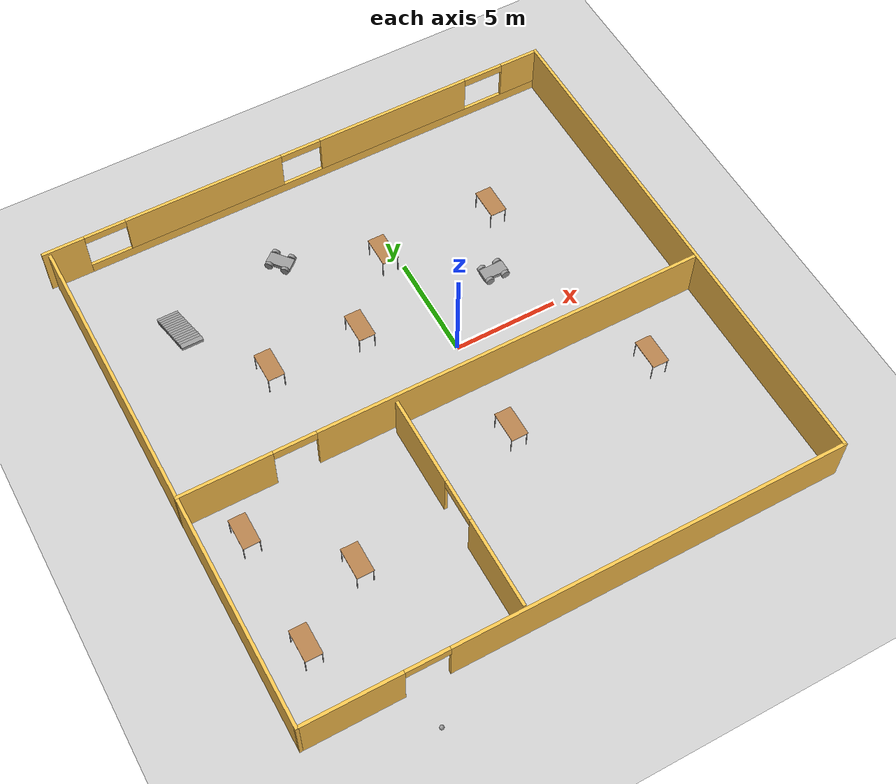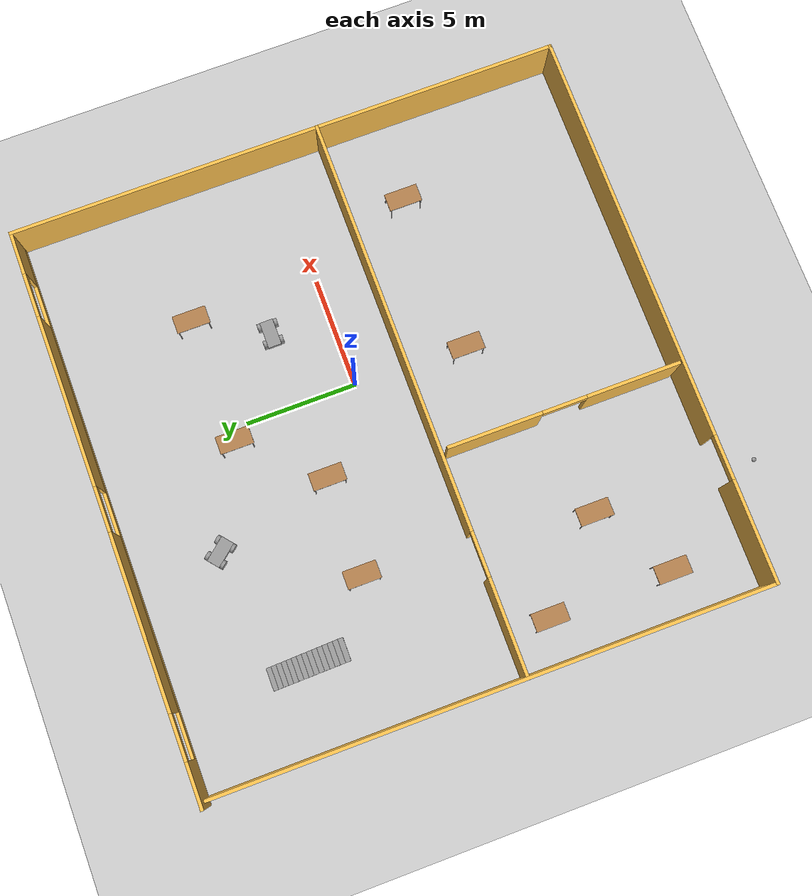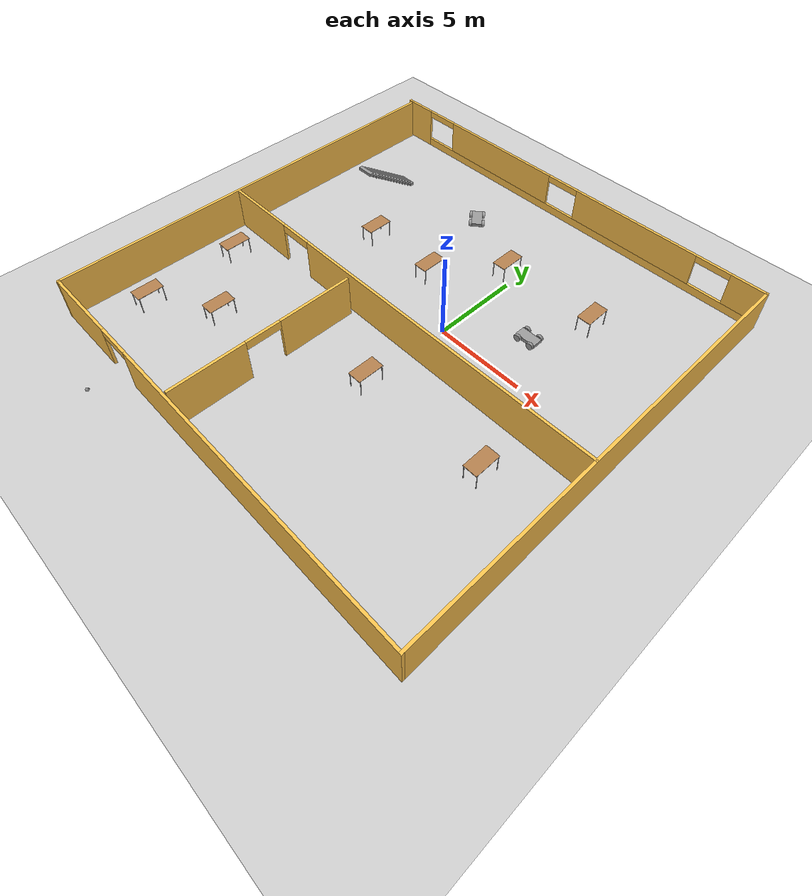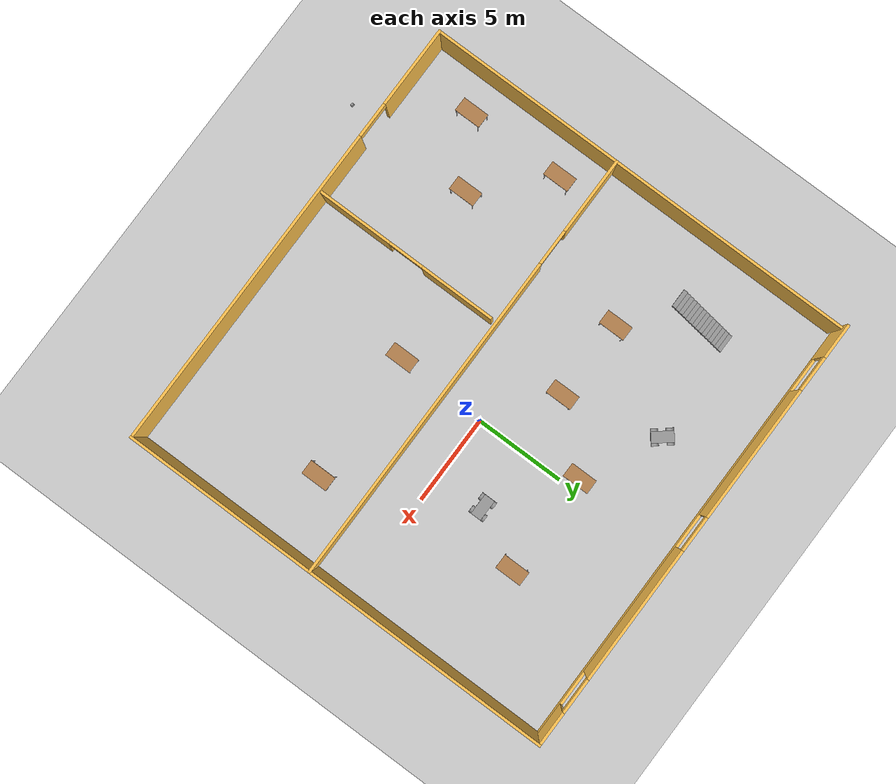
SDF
<sdf version="1.6">
 <world name="default">
  <plugin name="hello" filename="libhello.so"/>
  <light name="sun" type="directional">
   <pose>0 0 10 0 -0 0</pose>
   <diffuse>0.8 0.8 0.8 1</diffuse>
   <specular>0.2 0.2 0.2 1</specular>
   <attenuation>
    <range>1000</range>
    <constant>0.9</constant>
    <linear>0.01</linear>
    <quadratic>0.001</quadratic>
   </attenuation>
   <direction>-0.5 0.1 -0.9</direction>
  </light>
  <model name="ground_plane">
   <static>1</static>
   <link name="link">
    <collision name="collision">
     <geometry><plane><normal>0 0 1</normal><size>100 100</size></plane></geometry>
     <surface>
      <contact><collide_bitmask>65535</collide_bitmask></contact>
      <friction><ode><mu>100</mu><mu2>50</mu2></ode></friction>
     </surface>
    </collision>
    <visual name="visual">
     <cast_shadows>0</cast_shadows>
     <geometry><plane><normal>0 0 1</normal><size>100 100</size></plane></geometry>
     <material>
      <script><uri>file://media/materials/scripts/gazebo.material</uri><name>Gazebo/Grey</name></script>
     </material>
    </visual>
   </link>
  </model>
  <gravity>0 0 -9.8</gravity>
  <magnetic_field>6e-06 2.3e-05 -4.2e-05</magnetic_field>
  <atmosphere type="adiabatic"/>
  <physics name="default_physics" default="0" type="ode">
   <max_step_size>0.001</max_step_size>
   <real_time_factor>1</real_time_factor>
   <real_time_update_rate>1000</real_time_update_rate>
  </physics>
  <scene><ambient>0.4 0.4 0.4 1</ambient><background>0.7 0.7 0.7 1</background><shadows>1</shadows></scene>
  <spherical_coordinates>
   <surface_model>EARTH_WGS84</surface_model>
   <latitude_deg>0</latitude_deg>
   <longitude_deg>0</longitude_deg>
   <elevation>0</elevation>
   <heading_deg>0</heading_deg>
  </spherical_coordinates>
  <model name="table">
   <static>1</static>
   <link name="link">
    <collision name="surface">
     <pose>0 0 1 0 -0 0</pose>
     <geometry><box><size>1.5 0.8 0.03</size></box></geometry>
     <surface><friction><ode><mu>0.6</mu><mu2>0.6</mu2></ode></friction></surface>
    </collision>
    <visual name="visual1">
     <pose>0 0 1 0 -0 0</pose>
     <geometry><box><size>1.5 0.8 0.03</size></box></geometry>
     <material>
      <script><uri>file://media/materials/scripts/gazebo.material</uri><name>Gazebo/Wood</name></script>
     </material>
    </visual>
    <collision name="front_left_leg">
     <pose>0.68 0.38 0.5 0 -0 0</pose>
     <geometry><cylinder><radius>0.02</radius><length>1</length></cylinder></geometry>
    </collision>
    <visual name="front_left_leg">
     <pose>0.68 0.38 0.5 0 -0 0</pose>
     <geometry><cylinder><radius>0.02</radius><length>1</length></cylinder></geometry>
     <material>
      <script><uri>file://media/materials/scripts/gazebo.material</uri><name>Gazebo/Grey</name></script>
     </material>
    </visual>
    <collision name="front_right_leg">
     <pose>0.68 -0.38 0.5 0 -0 0</pose>
     <geometry><cylinder><radius>0.02</radius><length>1</length></cylinder></geometry>
    </collision>
    <visual name="front_right_leg">
     <pose>0.68 -0.38 0.5 0 -0 0</pose>
     <geometry><cylinder><radius>0.02</radius><length>1</length></cylinder></geometry>
     <material>
      <script><uri>file://media/materials/scripts/gazebo.material</uri><name>Gazebo/Grey</name></script>
     </material>
    </visual>
    <collision name="back_right_leg">
     <pose>-0.68 -0.38 0.5 0 -0 0</pose>
     <geometry><cylinder><radius>0.02</radius><length>1</length></cylinder></geometry>
    </collision>
    <visual name="back_right_leg">
     <pose>-0.68 -0.38 0.5 0 -0 0</pose>
     <geometry><cylinder><radius>0.02</radius><length>1</length></cylinder></geometry>
     <material>
      <script><uri>file://media/materials/scripts/gazebo.material</uri><name>Gazebo/Grey</name></script>
     </material>
    </visual>
    <collision name="back_left_leg">
     <pose>-0.68 0.38 0.5 0 -0 0</pose>
     <geometry><cylinder><radius>0.02</radius><length>1</length></cylinder></geometry>
    </collision>
    <visual name="back_left_leg">
     <pose>-0.68 0.38 0.5 0 -0 0</pose>
     <geometry><cylinder><radius>0.02</radius><length>1</length></cylinder></geometry>
     <material>
      <script><uri>file://media/materials/scripts/gazebo.material</uri><name>Gazebo/Grey</name></script>
     </material>
    </visual>
   </link>
   <pose>4.98532 5.74806 0 0 -0 1.5708</pose>
  </model>
  <model name="table_0">
   <static>1</static>
   <link name="link">
    <collision name="surface">
     <pose>0 0 1 0 -0 0</pose>
     <geometry><box><size>1.5 0.8 0.03</size></box></geometry>
     <surface><friction><ode><mu>0.6</mu><mu2>0.6</mu2></ode></friction></surface>
    </collision>
    <visual name="visual1">
     <pose>0 0 1 0 -0 0</pose>
     <geometry><box><size>1.5 0.8 0.03</size></box></geometry>
     <material>
      <script><uri>file://media/materials/scripts/gazebo.material</uri><name>Gazebo/Wood</name></script>
     </material>
    </visual>
    <collision name="front_left_leg">
     <pose>0.68 0.38 0.5 0 -0 0</pose>
     <geometry><cylinder><radius>0.02</radius><length>1</length></cylinder></geometry>
    </collision>
    <visual name="front_left_leg">
     <pose>0.68 0.38 0.5 0 -0 0</pose>
     <geometry><cylinder><radius>0.02</radius><length>1</length></cylinder></geometry>
     <material>
      <script><uri>file://media/materials/scripts/gazebo.material</uri><name>Gazebo/Grey</name></script>
     </material>
    </visual>
    <collision name="front_right_leg">
     <pose>0.68 -0.38 0.5 0 -0 0</pose>
     <geometry><cylinder><radius>0.02</radius><length>1</length></cylinder></geometry>
    </collision>
    <visual name="front_right_leg">
     <pose>0.68 -0.38 0.5 0 -0 0</pose>
     <geometry><cylinder><radius>0.02</radius><length>1</length></cylinder></geometry>
     <material>
      <script><uri>file://media/materials/scripts/gazebo.material</uri><name>Gazebo/Grey</name></script>
     </material>
    </visual>
    <collision name="back_right_leg">
     <pose>-0.68 -0.38 0.5 0 -0 0</pose>
     <geometry><cylinder><radius>0.02</radius><length>1</length></cylinder></geometry>
    </collision>
    <visual name="back_right_leg">
     <pose>-0.68 -0.38 0.5 0 -0 0</pose>
     <geometry><cylinder><radius>0.02</radius><length>1</length></cylinder></geometry>
     <material>
      <script><uri>file://media/materials/scripts/gazebo.material</uri><name>Gazebo/Grey</name></script>
     </material>
    </visual>
    <collision name="back_left_leg">
     <pose>-0.68 0.38 0.5 0 -0 0</pose>
     <geometry><cylinder><radius>0.02</radius><length>1</length></cylinder></geometry>
    </collision>
    <visual name="back_left_leg">
     <pose>-0.68 0.38 0.5 0 -0 0</pose>
     <geometry><cylinder><radius>0.02</radius><length>1</length></cylinder></geometry>
     <material>
      <script><uri>file://media/materials/scripts/gazebo.material</uri><name>Gazebo/Grey</name></script>
     </material>
    </visual>
   </link>
   <pose>-0.681354 5.72212 0 0 -0 1.5708</pose>
  </model>
  <model name="building_0">
   <pose>-1.83631 -0.712175 0 0 -0 0</pose>
   <link name="Stairs_0">
    <visual name="Stairs_0_Visual_0">
     <pose>-8.80586 8.30072 0.083333 0 -0 0</pose>
     <geometry><box><size>1 0.233333 0.166667</size></box></geometry>
     <material>
      <script><uri>file://media/materials/scripts/gazebo.material</uri><name>Gazebo/Grey</name></script>
      <ambient>1 1 1 1</ambient>
     </material>
     <meta><layer>0</layer></meta>
    </visual>
    <collision name="Stairs_0_Collision_0">
     <geometry><box><size>1 0.233333 0.166667</size></box></geometry>
     <pose>-8.80586 8.30072 0.083333 0 -0 0</pose>
    </collision>
    <visual name="Stairs_0_Visual_1">
     <pose>-8.80586 8.06739 0.25 0 -0 0</pose>
     <geometry><box><size>1 0.233333 0.166667</size></box></geometry>
     <material>
      <script><uri>file://media/materials/scripts/gazebo.material</uri><name>Gazebo/Grey</name></script>
      <ambient>1 1 1 1</ambient>
     </material>
     <meta><layer>0</layer></meta>
    </visual>
    <collision name="Stairs_0_Collision_1">
     <geometry><box><size>1 0.233333 0.166667</size></box></geometry>
     <pose>-8.80586 8.06739 0.25 0 -0 0</pose>
    </collision>
    <visual name="Stairs_0_Visual_2">
     <pose>-8.80586 7.83406 0.416667 0 -0 0</pose>
     <geometry><box><size>1 0.233333 0.166667</size></box></geometry>
     <material>
      <script><uri>file://media/materials/scripts/gazebo.material</uri><name>Gazebo/Grey</name></script>
      <ambient>1 1 1 1</ambient>
     </material>
     <meta><layer>0</layer></meta>
    </visual>
    <collision name="Stairs_0_Collision_2">
     <geometry><box><size>1 0.233333 0.166667</size></box></geometry>
     <pose>-8.80586 7.83406 0.416667 0 -0 0</pose>
    </collision>
    <visual name="Stairs_0_Visual_3">
     <pose>-8.80586 7.60072 0.583333 0 -0 0</pose>
     <geometry><box><size>1 0.233333 0.166667</size></box></geometry>
     <material>
      <script><uri>file://media/materials/scripts/gazebo.material</uri><name>Gazebo/Grey</name></script>
      <ambient>1 1 1 1</ambient>
     </material>
     <meta><layer>0</layer></meta>
    </visual>
    <collision name="Stairs_0_Collision_3">
     <geometry><box><size>1 0.233333 0.166667</size></box></geometry>
     <pose>-8.80586 7.60072 0.583333 0 -0 0</pose>
    </collision>
    <visual name="Stairs_0_Visual_4">
     <pose>-8.80586 7.36739 0.75 0 -0 0</pose>
     <geometry><box><size>1 0.233333 0.166667</size></box></geometry>
     <material>
      <script><uri>file://media/materials/scripts/gazebo.material</uri><name>Gazebo/Grey</name></script>
      <ambient>1 1 1 1</ambient>
     </material>
     <meta><layer>0</layer></meta>
    </visual>
    <collision name="Stairs_0_Collision_4">
     <geometry><box><size>1 0.233333 0.166667</size></box></geometry>
     <pose>-8.80586 7.36739 0.75 0 -0 0</pose>
    </collision>
    <visual name="Stairs_0_Visual_5">
     <pose>-8.80586 7.13406 0.916667 0 -0 0</pose>
     <geometry><box><size>1 0.233333 0.166667</size></box></geometry>
     <material>
      <script><uri>file://media/materials/scripts/gazebo.material</uri><name>Gazebo/Grey</name></script>
      <ambient>1 1 1 1</ambient>
     </material>
     <meta><layer>0</layer></meta>
    </visual>
    <collision name="Stairs_0_Collision_5">
     <geometry><box><size>1 0.233333 0.166667</size></box></geometry>
     <pose>-8.80586 7.13406 0.916667 0 -0 0</pose>
    </collision>
    <visual name="Stairs_0_Visual_6">
     <pose>-8.80586 6.90072 1.08333 0 -0 0</pose>
     <geometry><box><size>1 0.233333 0.166667</size></box></geometry>
     <material>
      <script><uri>file://media/materials/scripts/gazebo.material</uri><name>Gazebo/Grey</name></script>
      <ambient>1 1 1 1</ambient>
     </material>
     <meta><layer>0</layer></meta>
    </visual>
    <collision name="Stairs_0_Collision_6">
     <geometry><box><size>1 0.233333 0.166667</size></box></geometry>
     <pose>-8.80586 6.90072 1.08333 0 -0 0</pose>
    </collision>
    <visual name="Stairs_0_Visual_7">
     <pose>-8.80586 6.66739 1.25 0 -0 0</pose>
     <geometry><box><size>1 0.233333 0.166667</size></box></geometry>
     <material>
      <script><uri>file://media/materials/scripts/gazebo.material</uri><name>Gazebo/Grey</name></script>
      <ambient>1 1 1 1</ambient>
     </material>
     <meta><layer>0</layer></meta>
    </visual>
    <collision name="Stairs_0_Collision_7">
     <geometry><box><size>1 0.233333 0.166667</size></box></geometry>
     <pose>-8.80586 6.66739 1.25 0 -0 0</pose>
    </collision>
    <visual name="Stairs_0_Visual_8">
     <pose>-8.80586 6.43406 1.41667 0 -0 0</pose>
     <geometry><box><size>1 0.233333 0.166667</size></box></geometry>
     <material>
      <script><uri>file://media/materials/scripts/gazebo.material</uri><name>Gazebo/Grey</name></script>
      <ambient>1 1 1 1</ambient>
     </material>
     <meta><layer>0</layer></meta>
    </visual>
    <collision name="Stairs_0_Collision_8">
     <geometry><box><size>1 0.233333 0.166667</size></box></geometry>
     <pose>-8.80586 6.43406 1.41667 0 -0 0</pose>
    </collision>
    <visual name="Stairs_0_Visual_9">
     <pose>-8.80586 6.20072 1.58333 0 -0 0</pose>
     <geometry><box><size>1 0.233333 0.166667</size></box></geometry>
     <material>
      <script><uri>file://media/materials/scripts/gazebo.material</uri><name>Gazebo/Grey</name></script>
      <ambient>1 1 1 1</ambient>
     </material>
     <meta><layer>0</layer></meta>
    </visual>
    <collision name="Stairs_0_Collision_9">
     <geometry><box><size>1 0.233333 0.166667</size></box></geometry>
     <pose>-8.80586 6.20072 1.58333 0 -0 0</pose>
    </collision>
    <visual name="Stairs_0_Visual_10">
     <pose>-8.80586 5.96739 1.75 0 -0 0</pose>
     <geometry><box><size>1 0.233333 0.166667</size></box></geometry>
     <material>
      <script><uri>file://media/materials/scripts/gazebo.material</uri><name>Gazebo/Grey</name></script>
      <ambient>1 1 1 1</ambient>
     </material>
     <meta><layer>0</layer></meta>
    </visual>
    <collision name="Stairs_0_Collision_10">
     <geometry><box><size>1 0.233333 0.166667</size></box></geometry>
     <pose>-8.80586 5.96739 1.75 0 -0 0</pose>
    </collision>
    <visual name="Stairs_0_Visual_11">
     <pose>-8.80586 5.73406 1.91667 0 -0 0</pose>
     <geometry><box><size>1 0.233333 0.166667</size></box></geometry>
     <material>
      <script><uri>file://media/materials/scripts/gazebo.material</uri><name>Gazebo/Grey</name></script>
      <ambient>1 1 1 1</ambient>
     </material>
     <meta><layer>0</layer></meta>
    </visual>
    <collision name="Stairs_0_Collision_11">
     <geometry><box><size>1 0.233333 0.166667</size></box></geometry>
     <pose>-8.80586 5.73406 1.91667 0 -0 0</pose>
    </collision>
    <visual name="Stairs_0_Visual_12">
     <pose>-8.80586 5.50072 2.08333 0 -0 0</pose>
     <geometry><box><size>1 0.233333 0.166667</size></box></geometry>
     <material>
      <script><uri>file://media/materials/scripts/gazebo.material</uri><name>Gazebo/Grey</name></script>
      <ambient>1 1 1 1</ambient>
     </material>
     <meta><layer>0</layer></meta>
    </visual>
    <collision name="Stairs_0_Collision_12">
     <geometry><box><size>1 0.233333 0.166667</size></box></geometry>
     <pose>-8.80586 5.50072 2.08333 0 -0 0</pose>
    </collision>
    <visual name="Stairs_0_Visual_13">
     <pose>-8.80586 5.26739 2.25 0 -0 0</pose>
     <geometry><box><size>1 0.233333 0.166667</size></box></geometry>
     <material>
      <script><uri>file://media/materials/scripts/gazebo.material</uri><name>Gazebo/Grey</name></script>
      <ambient>1 1 1 1</ambient>
     </material>
     <meta><layer>0</layer></meta>
    </visual>
    <collision name="Stairs_0_Collision_13">
     <geometry><box><size>1 0.233333 0.166667</size></box></geometry>
     <pose>-8.80586 5.26739 2.25 0 -0 0</pose>
    </collision>
    <visual name="Stairs_0_Visual_14">
     <pose>-8.80586 5.03406 2.41667 0 -0 0</pose>
     <geometry><box><size>1 0.233333 0.166667</size></box></geometry>
     <material>
      <script><uri>file://media/materials/scripts/gazebo.material</uri><name>Gazebo/Grey</name></script>
      <ambient>1 1 1 1</ambient>
     </material>
     <meta><layer>0</layer></meta>
    </visual>
    <collision name="Stairs_0_Collision_14">
     <geometry><box><size>1 0.233333 0.166667</size></box></geometry>
     <pose>-8.80586 5.03406 2.41667 0 -0 0</pose>
    </collision>
   </link>
   <link name="Wall_0">
    <pose>-1e-06 12.425 0 0 -0 0</pose>
    <visual name="Wall_0_Visual_0">
     <pose>-11.7466 0 1.25 0 -0 0</pose>
     <geometry><box><size>2.0068 0.15 2.5</size></box></geometry>
     <material>
      <script><uri>file://media/materials/scripts/gazebo.material</uri><name>Gazebo/Grey</name></script>
      <ambient>1 0.764706 0.305882 1</ambient>
     </material>
     <meta><layer>0</layer></meta>
    </visual>
    <collision name="Wall_0_Collision_0">
     <geometry><box><size>2.0068 0.15 2.5</size></box></geometry>
     <pose>-11.7466 0 1.25 0 -0 0</pose>
    </collision>
    <visual name="Wall_0_Visual_1">
     <pose>1.0034 0 0.25 0 -0 0</pose>
     <geometry><box><size>23.4932 0.15 0.5</size></box></geometry>
     <material>
      <script><uri>file://media/materials/scripts/gazebo.material</uri><name>Gazebo/Grey</name></script>
      <ambient>1 0.764706 0.305882 1</ambient>
     </material>
     <meta><layer>0</layer></meta>
    </visual>
    <collision name="Wall_0_Collision_1">
     <geometry><box><size>23.4932 0.15 0.5</size></box></geometry>
     <pose>1.0034 0 0.25 0 -0 0</pose>
    </collision>
    <visual name="Wall_0_Visual_2">
     <pose>-4.86655 0 1.5 0 -0 0</pose>
     <geometry><box><size>7.75331 0.15 2</size></box></geometry>
     <material>
      <script><uri>file://media/materials/scripts/gazebo.material</uri><name>Gazebo/Grey</name></script>
      <ambient>1 0.764706 0.305882 1</ambient>
     </material>
     <meta><layer>0</layer></meta>
    </visual>
    <collision name="Wall_0_Collision_2">
     <geometry><box><size>7.75331 0.15 2</size></box></geometry>
     <pose>-4.86655 0 1.5 0 -0 0</pose>
    </collision>
    <visual name="Wall_0_Visual_3">
     <pose>4.87812 0 1.5 0 -0 0</pose>
     <geometry><box><size>7.73602 0.15 2</size></box></geometry>
     <material>
      <script><uri>file://media/materials/scripts/gazebo.material</uri><name>Gazebo/Grey</name></script>
      <ambient>1 0.764706 0.305882 1</ambient>
     </material>
     <meta><layer>0</layer></meta>
    </visual>
    <collision name="Wall_0_Collision_3">
     <geometry><box><size>7.73602 0.15 2</size></box></geometry>
     <pose>4.87812 0 1.5 0 -0 0</pose>
    </collision>
    <visual name="Wall_0_Visual_4">
     <pose>11.7481 0 1.5 0 -0 0</pose>
     <geometry><box><size>2.00387 0.15 2</size></box></geometry>
     <material>
      <script><uri>file://media/materials/scripts/gazebo.material</uri><name>Gazebo/Grey</name></script>
      <ambient>1 0.764706 0.305882 1</ambient>
     </material>
     <meta><layer>0</layer></meta>
    </visual>
    <collision name="Wall_0_Collision_4">
     <geometry><box><size>2.00387 0.15 2</size></box></geometry>
     <pose>11.7481 0 1.5 0 -0 0</pose>
    </collision>
    <visual name="Wall_0_Visual_5">
     <pose>-9.7432 0 2.3 0 -0 0</pose>
     <geometry><box><size>2 0.15 0.4</size></box></geometry>
     <material>
      <script><uri>file://media/materials/scripts/gazebo.material</uri><name>Gazebo/Grey</name></script>
      <ambient>1 0.764706 0.305882 1</ambient>
     </material>
     <meta><layer>0</layer></meta>
    </visual>
    <collision name="Wall_0_Collision_5">
     <geometry><box><size>2 0.15 0.4</size></box></geometry>
     <pose>-9.7432 0 2.3 0 -0 0</pose>
    </collision>
    <visual name="Wall_0_Visual_6">
     <pose>0.01011 0 2.3 0 -0 0</pose>
     <geometry><box><size>2 0.15 0.4</size></box></geometry>
     <material>
      <script><uri>file://media/materials/scripts/gazebo.material</uri><name>Gazebo/Grey</name></script>
      <ambient>1 0.764706 0.305882 1</ambient>
     </material>
     <meta><layer>0</layer></meta>
    </visual>
    <collision name="Wall_0_Collision_6">
     <geometry><box><size>2 0.15 0.4</size></box></geometry>
     <pose>0.01011 0 2.3 0 -0 0</pose>
    </collision>
    <visual name="Wall_0_Visual_7">
     <pose>9.74613 0 2.3 0 -0 0</pose>
     <geometry><box><size>2 0.15 0.4</size></box></geometry>
     <material>
      <script><uri>file://media/materials/scripts/gazebo.material</uri><name>Gazebo/Grey</name></script>
      <ambient>1 0.764706 0.305882 1</ambient>
     </material>
     <meta><layer>0</layer></meta>
    </visual>
    <collision name="Wall_0_Collision_7">
     <geometry><box><size>2 0.15 0.4</size></box></geometry>
     <pose>9.74613 0 2.3 0 -0 0</pose>
    </collision>
   </link>
   <link name="Wall_1">
    <collision name="Wall_1_Collision">
     <geometry><box><size>25 0.15 2.5</size></box></geometry>
     <pose>0 0 1.25 0 -0 0</pose>
    </collision>
    <visual name="Wall_1_Visual">
     <pose>0 0 1.25 0 -0 0</pose>
     <geometry><box><size>25 0.15 2.5</size></box></geometry>
     <material>
      <script><uri>file://media/materials/scripts/gazebo.material</uri><name>Gazebo/Grey</name></script>
      <ambient>1 0.764706 0.305882 1</ambient>
     </material>
     <meta><layer>0</layer></meta>
    </visual>
    <pose>12.675 0 0 0 0 -1.5708</pose>
   </link>
   <link name="Wall_2">
    <pose>0.124999 -12.425 0 0 -0 3.14159</pose>
    <visual name="Wall_2_Visual_0">
     <pose>-3.3109 0 1.25 0 -0 0</pose>
     <geometry><box><size>18.6282 0.15 2.5</size></box></geometry>
     <material>
      <script><uri>file://media/materials/scripts/gazebo.material</uri><name>Gazebo/Grey</name></script>
      <ambient>1 0.764706 0.305882 1</ambient>
     </material>
     <meta><layer>0</layer></meta>
    </visual>
    <collision name="Wall_2_Collision_0">
     <geometry><box><size>18.6282 0.15 2.5</size></box></geometry>
     <pose>-3.3109 0 1.25 0 -0 0</pose>
    </collision>
    <visual name="Wall_2_Visual_1">
     <pose>10.3141 0 1.25 0 -0 0</pose>
     <geometry><box><size>4.62181 0.15 2.5</size></box></geometry>
     <material>
      <script><uri>file://media/materials/scripts/gazebo.material</uri><name>Gazebo/Grey</name></script>
      <ambient>1 0.764706 0.305882 1</ambient>
     </material>
     <meta><layer>0</layer></meta>
    </visual>
    <collision name="Wall_2_Collision_1">
     <geometry><box><size>4.62181 0.15 2.5</size></box></geometry>
     <pose>10.3141 0 1.25 0 -0 0</pose>
    </collision>
    <visual name="Wall_2_Visual_2">
     <pose>7.00319 0 2.25 0 -0 0</pose>
     <geometry><box><size>2 0.15 0.5</size></box></geometry>
     <material>
      <script><uri>file://media/materials/scripts/gazebo.material</uri><name>Gazebo/Grey</name></script>
      <ambient>1 0.764706 0.305882 1</ambient>
     </material>
     <meta><layer>0</layer></meta>
    </visual>
    <collision name="Wall_2_Collision_2">
     <geometry><box><size>2 0.15 0.5</size></box></geometry>
     <pose>7.00319 0 2.25 0 -0 0</pose>
    </collision>
   </link>
   <link name="Wall_3">
    <collision name="Wall_3_Collision">
     <geometry><box><size>24.75 0.15 2.5</size></box></geometry>
     <pose>0 0 1.25 0 -0 0</pose>
    </collision>
    <visual name="Wall_3_Visual">
     <pose>0 0 1.25 0 -0 0</pose>
     <geometry><box><size>24.75 0.15 2.5</size></box></geometry>
     <material>
      <script><uri>file://media/materials/scripts/gazebo.material</uri><name>Gazebo/Grey</name></script>
      <ambient>1 0.764706 0.305882 1</ambient>
     </material>
     <meta><layer>0</layer></meta>
    </visual>
    <pose>-12.425 -0.125 0 0 -0 1.5708</pose>
   </link>
   <link name="Wall_5">
    <pose>0.118339 -1.50622 0 0 -0 0</pose>
    <visual name="Wall_5_Visual_0">
     <pose>-10.4316 0 1.25 0 -0 0</pose>
     <geometry><box><size>4.38678 0.15 2.5</size></box></geometry>
     <material>
      <script><uri>file://media/materials/scripts/gazebo.material</uri><name>Gazebo/Grey</name></script>
      <ambient>1 0.764706 0.305882 1</ambient>
     </material>
     <meta><layer>0</layer></meta>
    </visual>
    <collision name="Wall_5_Collision_0">
     <geometry><box><size>4.38678 0.15 2.5</size></box></geometry>
     <pose>-10.4316 0 1.25 0 -0 0</pose>
    </collision>
    <visual name="Wall_5_Visual_1">
     <pose>3.19339 0 1.25 0 -0 0</pose>
     <geometry><box><size>18.8632 0.15 2.5</size></box></geometry>
     <material>
      <script><uri>file://media/materials/scripts/gazebo.material</uri><name>Gazebo/Grey</name></script>
      <ambient>1 0.764706 0.305882 1</ambient>
     </material>
     <meta><layer>0</layer></meta>
    </visual>
    <collision name="Wall_5_Collision_1">
     <geometry><box><size>18.8632 0.15 2.5</size></box></geometry>
     <pose>3.19339 0 1.25 0 -0 0</pose>
    </collision>
    <visual name="Wall_5_Visual_2">
     <pose>-7.23822 0 2.25 0 -0 0</pose>
     <geometry><box><size>2 0.15 0.5</size></box></geometry>
     <material>
      <script><uri>file://media/materials/scripts/gazebo.material</uri><name>Gazebo/Grey</name></script>
      <ambient>1 0.764706 0.305882 1</ambient>
     </material>
     <meta><layer>0</layer></meta>
    </visual>
    <collision name="Wall_5_Collision_2">
     <geometry><box><size>2 0.15 0.5</size></box></geometry>
     <pose>-7.23822 0 2.25 0 -0 0</pose>
    </collision>
   </link>
   <link name="Wall_7">
    <pose>-2.51556 -7.04622 0 0 0 -1.5708</pose>
    <visual name="Wall_7_Visual_0">
     <pose>-3.12066 0 1.25 0 -0 0</pose>
     <geometry><box><size>4.25868 0.15 2.5</size></box></geometry>
     <material>
      <script><uri>file://media/materials/scripts/gazebo.material</uri><name>Gazebo/Grey</name></script>
      <ambient>1 0.764706 0.305882 1</ambient>
     </material>
     <meta><layer>0</layer></meta>
    </visual>
    <collision name="Wall_7_Collision_0">
     <geometry><box><size>4.25868 0.15 2.5</size></box></geometry>
     <pose>-3.12066 0 1.25 0 -0 0</pose>
    </collision>
    <visual name="Wall_7_Visual_1">
     <pose>3.12934 0 1.25 0 -0 0</pose>
     <geometry><box><size>4.24132 0.15 2.5</size></box></geometry>
     <material>
      <script><uri>file://media/materials/scripts/gazebo.material</uri><name>Gazebo/Grey</name></script>
      <ambient>1 0.764706 0.305882 1</ambient>
     </material>
     <meta><layer>0</layer></meta>
    </visual>
    <collision name="Wall_7_Collision_1">
     <geometry><box><size>4.24132 0.15 2.5</size></box></geometry>
     <pose>3.12934 0 1.25 0 -0 0</pose>
    </collision>
    <visual name="Wall_7_Visual_2">
     <pose>0.008684 0 2.25 0 -0 0</pose>
     <geometry><box><size>2 0.15 0.5</size></box></geometry>
     <material>
      <script><uri>file://media/materials/scripts/gazebo.material</uri><name>Gazebo/Grey</name></script>
      <ambient>1 0.764706 0.305882 1</ambient>
     </material>
     <meta><layer>0</layer></meta>
    </visual>
    <collision name="Wall_7_Collision_2">
     <geometry><box><size>2 0.15 0.5</size></box></geometry>
     <pose>0.008684 0 2.25 0 -0 0</pose>
    </collision>
   </link>
   <static>1</static>
  </model>
  <model name="robot">
   <link name="link_3">
    <pose>0 0 0.2 0 -0 0</pose>
    <inertial>
     <mass>1</mass>
     <inertia>
      <ixx>0.166667</ixx>
      <ixy>0</ixy>
      <ixz>0</ixz>
      <iyy>0.166667</iyy>
      <iyz>0</iyz>
      <izz>0.166667</izz>
     </inertia>
    </inertial>
    <visual name="visual">
     <geometry><box><size>1.2 0.6 0.2</size></box></geometry>
     <material>
      <lighting>1</lighting>
      <script><uri>file://media/materials/scripts/gazebo.material</uri><name>Gazebo/Grey</name></script>
      <shader type="pixel"><normal_map>__default__</normal_map></shader>
      <ambient>0.3 0.3 0.3 1</ambient>
      <diffuse>0.7 0.7 0.7 1</diffuse>
      <specular>0.01 0.01 0.01 1</specular>
      <emissive>0 0 0 1</emissive>
     </material>
    </visual>
    <collision name="collision">
     <geometry><box><size>1.2 0.6 0.2</size></box></geometry>
     <surface>
      <friction>
       <ode><mu>1</mu><mu2>1</mu2><fdir1>0 0 0</fdir1><slip1>0</slip1><slip2>0</slip2></ode>
       <torsional>
        <coefficient>1</coefficient>
        <patch_radius>0</patch_radius>
        <surface_radius>0</surface_radius>
        <use_patch_radius>1</use_patch_radius>
        <ode><slip>0</slip></ode>
       </torsional>
      </friction>
      <bounce><restitution_coefficient>0</restitution_coefficient><threshold>1e+06</threshold></bounce>
      <contact>
       <collide_without_contact>0</collide_without_contact>
       <collide_without_contact_bitmask>1</collide_without_contact_bitmask>
       <collide_bitmask>1</collide_bitmask>
       <ode>
        <soft_cfm>0</soft_cfm>
        <soft_erp>0.2</soft_erp>
        <kp>1e+13</kp>
        <kd>1</kd>
        <max_vel>0.01</max_vel>
        <min_depth>0</min_depth>
       </ode>
       <bullet>
        <split_impulse>1</split_impulse>
        <split_impulse_penetration_threshold>-0.01</split_impulse_penetration_threshold>
        <soft_cfm>0</soft_cfm>
        <soft_erp>0.2</soft_erp>
        <kp>1e+13</kp>
        <kd>1</kd>
       </bullet>
      </contact>
     </surface>
    </collision>
   </link>
   <link name="link_5_clone">
    <pose>-0.4 0.375001 0.2 1.5708 -0 0</pose>
    <inertial>
     <mass>1</mass>
     <inertia><ixx>0.145833</ixx><ixy>0</ixy><ixz>0</ixz><iyy>0.145833</iyy><iyz>0</iyz><izz>0.125</izz></inertia>
    </inertial>
    <visual name="visual">
     <geometry><cylinder><radius>0.2</radius><length>0.15</length></cylinder></geometry>
     <material>
      <lighting>1</lighting>
      <script><uri>file://media/materials/scripts/gazebo.material</uri><name>Gazebo/Grey</name></script>
      <shader type="pixel"><normal_map>__default__</normal_map></shader>
      <ambient>0.3 0.3 0.3 1</ambient>
      <diffuse>0.7 0.7 0.7 1</diffuse>
      <specular>0.01 0.01 0.01 1</specular>
      <emissive>0 0 0 1</emissive>
     </material>
    </visual>
    <collision name="collision">
     <geometry><cylinder><radius>0.2</radius><length>0.15</length></cylinder></geometry>
     <surface>
      <friction>
       <ode><mu>1</mu><mu2>1</mu2><fdir1>0 0 0</fdir1><slip1>0</slip1><slip2>0</slip2></ode>
       <torsional>
        <coefficient>1</coefficient>
        <patch_radius>0</patch_radius>
        <surface_radius>0</surface_radius>
        <use_patch_radius>1</use_patch_radius>
        <ode><slip>0</slip></ode>
       </torsional>
      </friction>
      <bounce><restitution_coefficient>0</restitution_coefficient><threshold>1e+06</threshold></bounce>
      <contact>
       <collide_without_contact>0</collide_without_contact>
       <collide_without_contact_bitmask>1</collide_without_contact_bitmask>
       <collide_bitmask>1</collide_bitmask>
       <ode>
        <soft_cfm>0</soft_cfm>
        <soft_erp>0.2</soft_erp>
        <kp>1e+13</kp>
        <kd>1</kd>
        <max_vel>0.01</max_vel>
        <min_depth>0</min_depth>
       </ode>
       <bullet>
        <split_impulse>1</split_impulse>
        <split_impulse_penetration_threshold>-0.01</split_impulse_penetration_threshold>
        <soft_cfm>0</soft_cfm>
        <soft_erp>0.2</soft_erp>
        <kp>1e+13</kp>
        <kd>1</kd>
       </bullet>
      </contact>
     </surface>
    </collision>
   </link>
   <link name="link_5_clone_0">
    <pose>-0.4 -0.375001 0.2 1.5708 -0 0</pose>
    <inertial>
     <mass>1</mass>
     <inertia><ixx>0.145833</ixx><ixy>0</ixy><ixz>0</ixz><iyy>0.145833</iyy><iyz>0</iyz><izz>0.125</izz></inertia>
    </inertial>
    <visual name="visual">
     <geometry><cylinder><radius>0.2</radius><length>0.15</length></cylinder></geometry>
     <material>
      <lighting>1</lighting>
      <script><uri>file://media/materials/scripts/gazebo.material</uri><name>Gazebo/Grey</name></script>
      <shader type="pixel"><normal_map>__default__</normal_map></shader>
      <ambient>0.3 0.3 0.3 1</ambient>
      <diffuse>0.7 0.7 0.7 1</diffuse>
      <specular>0.01 0.01 0.01 1</specular>
      <emissive>0 0 0 1</emissive>
     </material>
    </visual>
    <collision name="collision">
     <geometry><cylinder><radius>0.2</radius><length>0.15</length></cylinder></geometry>
     <surface>
      <friction>
       <ode><mu>1</mu><mu2>1</mu2><fdir1>0 0 0</fdir1><slip1>0</slip1><slip2>0</slip2></ode>
       <torsional>
        <coefficient>1</coefficient>
        <patch_radius>0</patch_radius>
        <surface_radius>0</surface_radius>
        <use_patch_radius>1</use_patch_radius>
        <ode><slip>0</slip></ode>
       </torsional>
      </friction>
      <bounce><restitution_coefficient>0</restitution_coefficient><threshold>1e+06</threshold></bounce>
      <contact>
       <collide_without_contact>0</collide_without_contact>
       <collide_without_contact_bitmask>1</collide_without_contact_bitmask>
       <collide_bitmask>1</collide_bitmask>
       <ode>
        <soft_cfm>0</soft_cfm>
        <soft_erp>0.2</soft_erp>
        <kp>1e+13</kp>
        <kd>1</kd>
        <max_vel>0.01</max_vel>
        <min_depth>0</min_depth>
       </ode>
       <bullet>
        <split_impulse>1</split_impulse>
        <split_impulse_penetration_threshold>-0.01</split_impulse_penetration_threshold>
        <soft_cfm>0</soft_cfm>
        <soft_erp>0.2</soft_erp>
        <kp>1e+13</kp>
        <kd>1</kd>
       </bullet>
      </contact>
     </surface>
    </collision>
   </link>
   <link name="link_5_clone_1">
    <pose>0.4 0.375001 0.2 1.5708 -0 0</pose>
    <inertial>
     <mass>1</mass>
     <inertia><ixx>0.145833</ixx><ixy>0</ixy><ixz>0</ixz><iyy>0.145833</iyy><iyz>0</iyz><izz>0.125</izz></inertia>
    </inertial>
    <visual name="visual">
     <geometry><cylinder><radius>0.2</radius><length>0.15</length></cylinder></geometry>
     <material>
      <lighting>1</lighting>
      <script><uri>file://media/materials/scripts/gazebo.material</uri><name>Gazebo/Grey</name></script>
      <shader type="pixel"><normal_map>__default__</normal_map></shader>
      <ambient>0.3 0.3 0.3 1</ambient>
      <diffuse>0.7 0.7 0.7 1</diffuse>
      <specular>0.01 0.01 0.01 1</specular>
      <emissive>0 0 0 1</emissive>
     </material>
    </visual>
    <collision name="collision">
     <geometry><cylinder><radius>0.2</radius><length>0.15</length></cylinder></geometry>
     <surface>
      <friction>
       <ode><mu>1</mu><mu2>1</mu2><fdir1>0 0 0</fdir1><slip1>0</slip1><slip2>0</slip2></ode>
       <torsional>
        <coefficient>1</coefficient>
        <patch_radius>0</patch_radius>
        <surface_radius>0</surface_radius>
        <use_patch_radius>1</use_patch_radius>
        <ode><slip>0</slip></ode>
       </torsional>
      </friction>
      <bounce><restitution_coefficient>0</restitution_coefficient><threshold>1e+06</threshold></bounce>
      <contact>
       <collide_without_contact>0</collide_without_contact>
       <collide_without_contact_bitmask>1</collide_without_contact_bitmask>
       <collide_bitmask>1</collide_bitmask>
       <ode>
        <soft_cfm>0</soft_cfm>
        <soft_erp>0.2</soft_erp>
        <kp>1e+13</kp>
        <kd>1</kd>
        <max_vel>0.01</max_vel>
        <min_depth>0</min_depth>
       </ode>
       <bullet>
        <split_impulse>1</split_impulse>
        <split_impulse_penetration_threshold>-0.01</split_impulse_penetration_threshold>
        <soft_cfm>0</soft_cfm>
        <soft_erp>0.2</soft_erp>
        <kp>1e+13</kp>
        <kd>1</kd>
       </bullet>
      </contact>
     </surface>
    </collision>
   </link>
   <link name="link_5_clone_2">
    <pose>0.4 -0.375001 0.2 1.5708 -0 0</pose>
    <inertial>
     <mass>1</mass>
     <inertia><ixx>0.145833</ixx><ixy>0</ixy><ixz>0</ixz><iyy>0.145833</iyy><iyz>0</iyz><izz>0.125</izz></inertia>
    </inertial>
    <visual name="visual">
     <geometry><cylinder><radius>0.2</radius><length>0.15</length></cylinder></geometry>
     <material>
      <lighting>1</lighting>
      <script><uri>file://media/materials/scripts/gazebo.material</uri><name>Gazebo/Grey</name></script>
      <shader type="pixel"><normal_map>__default__</normal_map></shader>
      <ambient>0.3 0.3 0.3 1</ambient>
      <diffuse>0.7 0.7 0.7 1</diffuse>
      <specular>0.01 0.01 0.01 1</specular>
      <emissive>0 0 0 1</emissive>
     </material>
    </visual>
    <collision name="collision">
     <geometry><cylinder><radius>0.2</radius><length>0.15</length></cylinder></geometry>
     <surface>
      <friction>
       <ode><mu>1</mu><mu2>1</mu2><fdir1>0 0 0</fdir1><slip1>0</slip1><slip2>0</slip2></ode>
       <torsional>
        <coefficient>1</coefficient>
        <patch_radius>0</patch_radius>
        <surface_radius>0</surface_radius>
        <use_patch_radius>1</use_patch_radius>
        <ode><slip>0</slip></ode>
       </torsional>
      </friction>
      <bounce><restitution_coefficient>0</restitution_coefficient><threshold>1e+06</threshold></bounce>
      <contact>
       <collide_without_contact>0</collide_without_contact>
       <collide_without_contact_bitmask>1</collide_without_contact_bitmask>
       <collide_bitmask>1</collide_bitmask>
       <ode>
        <soft_cfm>0</soft_cfm>
        <soft_erp>0.2</soft_erp>
        <kp>1e+13</kp>
        <kd>1</kd>
        <max_vel>0.01</max_vel>
        <min_depth>0</min_depth>
       </ode>
       <bullet>
        <split_impulse>1</split_impulse>
        <split_impulse_penetration_threshold>-0.01</split_impulse_penetration_threshold>
        <soft_cfm>0</soft_cfm>
        <soft_erp>0.2</soft_erp>
        <kp>1e+13</kp>
        <kd>1</kd>
       </bullet>
      </contact>
     </surface>
    </collision>
   </link>
   <joint name="link_3_JOINT_2" type="revolute">
    <parent>link_3</parent>
    <child>link_5_clone</child>
    <axis>
     <xyz>1 0 0</xyz>
     <use_parent_model_frame>0</use_parent_model_frame>
     <limit>
      <lower>-1.79769e+308</lower>
      <upper>1.79769e+308</upper>
      <effort>-1</effort>
      <velocity>-1</velocity>
     </limit>
     <dynamics>
      <spring_reference>0</spring_reference>
      <spring_stiffness>0</spring_stiffness>
      <damping>0</damping>
     </dynamics>
    </axis>
    <physics>
     <ode><limit><cfm>0</cfm><erp>0.2</erp></limit><suspension><cfm>0</cfm><erp>0.2</erp></suspension></ode>
    </physics>
   </joint>
   <joint name="link_3_JOINT_3" type="revolute">
    <parent>link_3</parent>
    <child>link_5_clone_0</child>
    <axis>
     <xyz>1 0 0</xyz>
     <use_parent_model_frame>0</use_parent_model_frame>
     <limit>
      <lower>-1.79769e+308</lower>
      <upper>1.79769e+308</upper>
      <effort>-1</effort>
      <velocity>-1</velocity>
     </limit>
     <dynamics>
      <spring_reference>0</spring_reference>
      <spring_stiffness>0</spring_stiffness>
      <damping>0</damping>
     </dynamics>
    </axis>
    <physics>
     <ode><limit><cfm>0</cfm><erp>0.2</erp></limit><suspension><cfm>0</cfm><erp>0.2</erp></suspension></ode>
    </physics>
   </joint>
   <joint name="link_3_JOINT_4" type="revolute">
    <parent>link_3</parent>
    <child>link_5_clone_1</child>
    <axis>
     <xyz>1 0 0</xyz>
     <use_parent_model_frame>0</use_parent_model_frame>
     <limit>
      <lower>-1.79769e+308</lower>
      <upper>1.79769e+308</upper>
      <effort>-1</effort>
      <velocity>-1</velocity>
     </limit>
     <dynamics>
      <spring_reference>0</spring_reference>
      <spring_stiffness>0</spring_stiffness>
      <damping>0</damping>
     </dynamics>
    </axis>
    <physics>
     <ode><limit><cfm>0</cfm><erp>0.2</erp></limit><suspension><cfm>0</cfm><erp>0.2</erp></suspension></ode>
    </physics>
   </joint>
   <joint name="link_3_JOINT_5" type="revolute">
    <parent>link_3</parent>
    <child>link_5_clone_2</child>
    <axis>
     <xyz>1 0 0</xyz>
     <use_parent_model_frame>0</use_parent_model_frame>
     <limit>
      <lower>-1.79769e+308</lower>
      <upper>1.79769e+308</upper>
      <effort>-1</effort>
      <velocity>-1</velocity>
     </limit>
     <dynamics>
      <spring_reference>0</spring_reference>
      <spring_stiffness>0</spring_stiffness>
      <damping>0</damping>
     </dynamics>
    </axis>
    <physics>
     <ode><limit><cfm>0</cfm><erp>0.2</erp></limit><suspension><cfm>0</cfm><erp>0.2</erp></suspension></ode>
    </physics>
   </joint>
   <static>0</static>
   <pose>-4.88928 7.88686 -6e-06 -1e-05 5e-06 -0.875028</pose>
  </model>
  <model name="robot_0">
   <link name="link_3">
    <pose>0 0 0.2 0 -0 0</pose>
    <inertial>
     <mass>1</mass>
     <inertia>
      <ixx>0.166667</ixx>
      <ixy>0</ixy>
      <ixz>0</ixz>
      <iyy>0.166667</iyy>
      <iyz>0</iyz>
      <izz>0.166667</izz>
     </inertia>
    </inertial>
    <visual name="visual">
     <geometry><box><size>1.2 0.6 0.2</size></box></geometry>
     <material>
      <lighting>1</lighting>
      <script><uri>file://media/materials/scripts/gazebo.material</uri><name>Gazebo/Grey</name></script>
      <shader type="pixel"><normal_map>__default__</normal_map></shader>
      <ambient>0.3 0.3 0.3 1</ambient>
      <diffuse>0.7 0.7 0.7 1</diffuse>
      <specular>0.01 0.01 0.01 1</specular>
      <emissive>0 0 0 1</emissive>
     </material>
    </visual>
    <collision name="collision">
     <geometry><box><size>1.2 0.6 0.2</size></box></geometry>
     <surface>
      <friction>
       <ode><mu>1</mu><mu2>1</mu2><fdir1>0 0 0</fdir1><slip1>0</slip1><slip2>0</slip2></ode>
       <torsional>
        <coefficient>1</coefficient>
        <patch_radius>0</patch_radius>
        <surface_radius>0</surface_radius>
        <use_patch_radius>1</use_patch_radius>
        <ode><slip>0</slip></ode>
       </torsional>
      </friction>
      <bounce><restitution_coefficient>0</restitution_coefficient><threshold>1e+06</threshold></bounce>
      <contact>
       <collide_without_contact>0</collide_without_contact>
       <collide_without_contact_bitmask>1</collide_without_contact_bitmask>
       <collide_bitmask>1</collide_bitmask>
       <ode>
        <soft_cfm>0</soft_cfm>
        <soft_erp>0.2</soft_erp>
        <kp>1e+13</kp>
        <kd>1</kd>
        <max_vel>0.01</max_vel>
        <min_depth>0</min_depth>
       </ode>
       <bullet>
        <split_impulse>1</split_impulse>
        <split_impulse_penetration_threshold>-0.01</split_impulse_penetration_threshold>
        <soft_cfm>0</soft_cfm>
        <soft_erp>0.2</soft_erp>
        <kp>1e+13</kp>
        <kd>1</kd>
       </bullet>
      </contact>
     </surface>
    </collision>
   </link>
   <link name="link_5_clone">
    <pose>-0.4 0.375001 0.2 1.5708 -0 0</pose>
    <inertial>
     <mass>1</mass>
     <inertia><ixx>0.145833</ixx><ixy>0</ixy><ixz>0</ixz><iyy>0.145833</iyy><iyz>0</iyz><izz>0.125</izz></inertia>
    </inertial>
    <visual name="visual">
     <geometry><cylinder><radius>0.2</radius><length>0.15</length></cylinder></geometry>
     <material>
      <lighting>1</lighting>
      <script><uri>file://media/materials/scripts/gazebo.material</uri><name>Gazebo/Grey</name></script>
      <shader type="pixel"><normal_map>__default__</normal_map></shader>
      <ambient>0.3 0.3 0.3 1</ambient>
      <diffuse>0.7 0.7 0.7 1</diffuse>
      <specular>0.01 0.01 0.01 1</specular>
      <emissive>0 0 0 1</emissive>
     </material>
    </visual>
    <collision name="collision">
     <geometry><cylinder><radius>0.2</radius><length>0.15</length></cylinder></geometry>
     <surface>
      <friction>
       <ode><mu>1</mu><mu2>1</mu2><fdir1>0 0 0</fdir1><slip1>0</slip1><slip2>0</slip2></ode>
       <torsional>
        <coefficient>1</coefficient>
        <patch_radius>0</patch_radius>
        <surface_radius>0</surface_radius>
        <use_patch_radius>1</use_patch_radius>
        <ode><slip>0</slip></ode>
       </torsional>
      </friction>
      <bounce><restitution_coefficient>0</restitution_coefficient><threshold>1e+06</threshold></bounce>
      <contact>
       <collide_without_contact>0</collide_without_contact>
       <collide_without_contact_bitmask>1</collide_without_contact_bitmask>
       <collide_bitmask>1</collide_bitmask>
       <ode>
        <soft_cfm>0</soft_cfm>
        <soft_erp>0.2</soft_erp>
        <kp>1e+13</kp>
        <kd>1</kd>
        <max_vel>0.01</max_vel>
        <min_depth>0</min_depth>
       </ode>
       <bullet>
        <split_impulse>1</split_impulse>
        <split_impulse_penetration_threshold>-0.01</split_impulse_penetration_threshold>
        <soft_cfm>0</soft_cfm>
        <soft_erp>0.2</soft_erp>
        <kp>1e+13</kp>
        <kd>1</kd>
       </bullet>
      </contact>
     </surface>
    </collision>
   </link>
   <link name="link_5_clone_0">
    <pose>-0.4 -0.375001 0.2 1.5708 -0 0</pose>
    <inertial>
     <mass>1</mass>
     <inertia><ixx>0.145833</ixx><ixy>0</ixy><ixz>0</ixz><iyy>0.145833</iyy><iyz>0</iyz><izz>0.125</izz></inertia>
    </inertial>
    <visual name="visual">
     <geometry><cylinder><radius>0.2</radius><length>0.15</length></cylinder></geometry>
     <material>
      <lighting>1</lighting>
      <script><uri>file://media/materials/scripts/gazebo.material</uri><name>Gazebo/Grey</name></script>
      <shader type="pixel"><normal_map>__default__</normal_map></shader>
      <ambient>0.3 0.3 0.3 1</ambient>
      <diffuse>0.7 0.7 0.7 1</diffuse>
      <specular>0.01 0.01 0.01 1</specular>
      <emissive>0 0 0 1</emissive>
     </material>
    </visual>
    <collision name="collision">
     <geometry><cylinder><radius>0.2</radius><length>0.15</length></cylinder></geometry>
     <surface>
      <friction>
       <ode><mu>1</mu><mu2>1</mu2><fdir1>0 0 0</fdir1><slip1>0</slip1><slip2>0</slip2></ode>
       <torsional>
        <coefficient>1</coefficient>
        <patch_radius>0</patch_radius>
        <surface_radius>0</surface_radius>
        <use_patch_radius>1</use_patch_radius>
        <ode><slip>0</slip></ode>
       </torsional>
      </friction>
      <bounce><restitution_coefficient>0</restitution_coefficient><threshold>1e+06</threshold></bounce>
      <contact>
       <collide_without_contact>0</collide_without_contact>
       <collide_without_contact_bitmask>1</collide_without_contact_bitmask>
       <collide_bitmask>1</collide_bitmask>
       <ode>
        <soft_cfm>0</soft_cfm>
        <soft_erp>0.2</soft_erp>
        <kp>1e+13</kp>
        <kd>1</kd>
        <max_vel>0.01</max_vel>
        <min_depth>0</min_depth>
       </ode>
       <bullet>
        <split_impulse>1</split_impulse>
        <split_impulse_penetration_threshold>-0.01</split_impulse_penetration_threshold>
        <soft_cfm>0</soft_cfm>
        <soft_erp>0.2</soft_erp>
        <kp>1e+13</kp>
        <kd>1</kd>
       </bullet>
      </contact>
     </surface>
    </collision>
   </link>
   <link name="link_5_clone_1">
    <pose>0.4 0.375001 0.2 1.5708 -0 0</pose>
    <inertial>
     <mass>1</mass>
     <inertia><ixx>0.145833</ixx><ixy>0</ixy><ixz>0</ixz><iyy>0.145833</iyy><iyz>0</iyz><izz>0.125</izz></inertia>
    </inertial>
    <visual name="visual">
     <geometry><cylinder><radius>0.2</radius><length>0.15</length></cylinder></geometry>
     <material>
      <lighting>1</lighting>
      <script><uri>file://media/materials/scripts/gazebo.material</uri><name>Gazebo/Grey</name></script>
      <shader type="pixel"><normal_map>__default__</normal_map></shader>
      <ambient>0.3 0.3 0.3 1</ambient>
      <diffuse>0.7 0.7 0.7 1</diffuse>
      <specular>0.01 0.01 0.01 1</specular>
      <emissive>0 0 0 1</emissive>
     </material>
    </visual>
    <collision name="collision">
     <geometry><cylinder><radius>0.2</radius><length>0.15</length></cylinder></geometry>
     <surface>
      <friction>
       <ode><mu>1</mu><mu2>1</mu2><fdir1>0 0 0</fdir1><slip1>0</slip1><slip2>0</slip2></ode>
       <torsional>
        <coefficient>1</coefficient>
        <patch_radius>0</patch_radius>
        <surface_radius>0</surface_radius>
        <use_patch_radius>1</use_patch_radius>
        <ode><slip>0</slip></ode>
       </torsional>
      </friction>
      <bounce><restitution_coefficient>0</restitution_coefficient><threshold>1e+06</threshold></bounce>
      <contact>
       <collide_without_contact>0</collide_without_contact>
       <collide_without_contact_bitmask>1</collide_without_contact_bitmask>
       <collide_bitmask>1</collide_bitmask>
       <ode>
        <soft_cfm>0</soft_cfm>
        <soft_erp>0.2</soft_erp>
        <kp>1e+13</kp>
        <kd>1</kd>
        <max_vel>0.01</max_vel>
        <min_depth>0</min_depth>
       </ode>
       <bullet>
        <split_impulse>1</split_impulse>
        <split_impulse_penetration_threshold>-0.01</split_impulse_penetration_threshold>
        <soft_cfm>0</soft_cfm>
        <soft_erp>0.2</soft_erp>
        <kp>1e+13</kp>
        <kd>1</kd>
       </bullet>
      </contact>
     </surface>
    </collision>
   </link>
   <link name="link_5_clone_2">
    <pose>0.4 -0.375001 0.2 1.5708 -0 0</pose>
    <inertial>
     <mass>1</mass>
     <inertia><ixx>0.145833</ixx><ixy>0</ixy><ixz>0</ixz><iyy>0.145833</iyy><iyz>0</iyz><izz>0.125</izz></inertia>
    </inertial>
    <visual name="visual">
     <geometry><cylinder><radius>0.2</radius><length>0.15</length></cylinder></geometry>
     <material>
      <lighting>1</lighting>
      <script><uri>file://media/materials/scripts/gazebo.material</uri><name>Gazebo/Grey</name></script>
      <shader type="pixel"><normal_map>__default__</normal_map></shader>
      <ambient>0.3 0.3 0.3 1</ambient>
      <diffuse>0.7 0.7 0.7 1</diffuse>
      <specular>0.01 0.01 0.01 1</specular>
      <emissive>0 0 0 1</emissive>
     </material>
    </visual>
    <collision name="collision">
     <geometry><cylinder><radius>0.2</radius><length>0.15</length></cylinder></geometry>
     <surface>
      <friction>
       <ode><mu>1</mu><mu2>1</mu2><fdir1>0 0 0</fdir1><slip1>0</slip1><slip2>0</slip2></ode>
       <torsional>
        <coefficient>1</coefficient>
        <patch_radius>0</patch_radius>
        <surface_radius>0</surface_radius>
        <use_patch_radius>1</use_patch_radius>
        <ode><slip>0</slip></ode>
       </torsional>
      </friction>
      <bounce><restitution_coefficient>0</restitution_coefficient><threshold>1e+06</threshold></bounce>
      <contact>
       <collide_without_contact>0</collide_without_contact>
       <collide_without_contact_bitmask>1</collide_without_contact_bitmask>
       <collide_bitmask>1</collide_bitmask>
       <ode>
        <soft_cfm>0</soft_cfm>
        <soft_erp>0.2</soft_erp>
        <kp>1e+13</kp>
        <kd>1</kd>
        <max_vel>0.01</max_vel>
        <min_depth>0</min_depth>
       </ode>
       <bullet>
        <split_impulse>1</split_impulse>
        <split_impulse_penetration_threshold>-0.01</split_impulse_penetration_threshold>
        <soft_cfm>0</soft_cfm>
        <soft_erp>0.2</soft_erp>
        <kp>1e+13</kp>
        <kd>1</kd>
       </bullet>
      </contact>
     </surface>
    </collision>
   </link>
   <joint name="link_3_JOINT_2" type="revolute">
    <parent>link_3</parent>
    <child>link_5_clone</child>
    <axis>
     <xyz>1 0 0</xyz>
     <use_parent_model_frame>0</use_parent_model_frame>
     <limit>
      <lower>-1.79769e+308</lower>
      <upper>1.79769e+308</upper>
      <effort>-1</effort>
      <velocity>-1</velocity>
     </limit>
     <dynamics>
      <spring_reference>0</spring_reference>
      <spring_stiffness>0</spring_stiffness>
      <damping>0</damping>
     </dynamics>
    </axis>
    <physics>
     <ode><limit><cfm>0</cfm><erp>0.2</erp></limit><suspension><cfm>0</cfm><erp>0.2</erp></suspension></ode>
    </physics>
   </joint>
   <joint name="link_3_JOINT_3" type="revolute">
    <parent>link_3</parent>
    <child>link_5_clone_0</child>
    <axis>
     <xyz>1 0 0</xyz>
     <use_parent_model_frame>0</use_parent_model_frame>
     <limit>
      <lower>-1.79769e+308</lower>
      <upper>1.79769e+308</upper>
      <effort>-1</effort>
      <velocity>-1</velocity>
     </limit>
     <dynamics>
      <spring_reference>0</spring_reference>
      <spring_stiffness>0</spring_stiffness>
      <damping>0</damping>
     </dynamics>
    </axis>
    <physics>
     <ode><limit><cfm>0</cfm><erp>0.2</erp></limit><suspension><cfm>0</cfm><erp>0.2</erp></suspension></ode>
    </physics>
   </joint>
   <joint name="link_3_JOINT_4" type="revolute">
    <parent>link_3</parent>
    <child>link_5_clone_1</child>
    <axis>
     <xyz>1 0 0</xyz>
     <use_parent_model_frame>0</use_parent_model_frame>
     <limit>
      <lower>-1.79769e+308</lower>
      <upper>1.79769e+308</upper>
      <effort>-1</effort>
      <velocity>-1</velocity>
     </limit>
     <dynamics>
      <spring_reference>0</spring_reference>
      <spring_stiffness>0</spring_stiffness>
      <damping>0</damping>
     </dynamics>
    </axis>
    <physics>
     <ode><limit><cfm>0</cfm><erp>0.2</erp></limit><suspension><cfm>0</cfm><erp>0.2</erp></suspension></ode>
    </physics>
   </joint>
   <joint name="link_3_JOINT_5" type="revolute">
    <parent>link_3</parent>
    <child>link_5_clone_2</child>
    <axis>
     <xyz>1 0 0</xyz>
     <use_parent_model_frame>0</use_parent_model_frame>
     <limit>
      <lower>-1.79769e+308</lower>
      <upper>1.79769e+308</upper>
      <effort>-1</effort>
      <velocity>-1</velocity>
     </limit>
     <dynamics>
      <spring_reference>0</spring_reference>
      <spring_stiffness>0</spring_stiffness>
      <damping>0</damping>
     </dynamics>
    </axis>
    <physics>
     <ode><limit><cfm>0</cfm><erp>0.2</erp></limit><suspension><cfm>0</cfm><erp>0.2</erp></suspension></ode>
    </physics>
   </joint>
   <static>0</static>
   <pose>3.4053 2.71957 0 0 -0 0.000101</pose>
  </model>
  <model name="my_ball">
   <link name="link_0">
    <inertial>
     <mass>1</mass>
     <inertia><ixx>0.1</ixx><ixy>0</ixy><ixz>0</ixz><iyy>0.1</iyy><iyz>0</iyz><izz>0.1</izz></inertia>
    </inertial>
    <visual name="visual">
     <geometry><sphere><radius>0.1</radius></sphere></geometry>
     <material>
      <lighting>1</lighting>
      <script><uri>file://media/materials/scripts/gazebo.material</uri><name>Gazebo/Grey</name></script>
      <shader type="pixel"><normal_map>__default__</normal_map></shader>
      <ambient>1 1 1 1</ambient>
      <diffuse>1 1 1 1</diffuse>
      <specular>1 1 1 1</specular>
      <emissive>1 1 1 1</emissive>
     </material>
    </visual>
    <collision name="collision">
     <geometry><sphere><radius>0.1</radius></sphere></geometry>
     <surface>
      <friction>
       <ode><mu>1</mu><mu2>1</mu2><fdir1>0 0 0</fdir1><slip1>0</slip1><slip2>0</slip2></ode>
       <torsional>
        <coefficient>1</coefficient>
        <patch_radius>0</patch_radius>
        <surface_radius>0</surface_radius>
        <use_patch_radius>1</use_patch_radius>
        <ode><slip>0</slip></ode>
       </torsional>
      </friction>
      <bounce><restitution_coefficient>0</restitution_coefficient><threshold>1e+06</threshold></bounce>
      <contact>
       <collide_without_contact>0</collide_without_contact>
       <collide_without_contact_bitmask>1</collide_without_contact_bitmask>
       <collide_bitmask>1</collide_bitmask>
       <ode>
        <soft_cfm>0</soft_cfm>
        <soft_erp>0.2</soft_erp>
        <kp>1e+13</kp>
        <kd>1</kd>
        <max_vel>0.01</max_vel>
        <min_depth>0</min_depth>
       </ode>
       <bullet>
        <split_impulse>1</split_impulse>
        <split_impulse_penetration_threshold>-0.01</split_impulse_penetration_threshold>
        <soft_cfm>0</soft_cfm>
        <soft_erp>0.2</soft_erp>
        <kp>1e+13</kp>
        <kd>1</kd>
       </bullet>
      </contact>
     </surface>
    </collision>
   </link>
   <static>0</static>
   <pose>-9.09504 -14.986 0.1 0 -0 0</pose>
  </model>
  <model name="table_clone">
   <static>1</static>
   <link name="link">
    <collision name="surface">
     <pose>0 0 1 0 -0 0</pose>
     <geometry><box><size>1.5 0.8 0.03</size></box></geometry>
     <surface><friction><ode><mu>0.6</mu><mu2>0.6</mu2></ode></friction></surface>
    </collision>
    <visual name="visual1">
     <pose>0 0 1 0 -0 0</pose>
     <geometry><box><size>1.5 0.8 0.03</size></box></geometry>
     <material>
      <script><uri>file://media/materials/scripts/gazebo.material</uri><name>Gazebo/Wood</name></script>
     </material>
    </visual>
    <collision name="front_left_leg">
     <pose>0.68 0.38 0.5 0 -0 0</pose>
     <geometry><cylinder><radius>0.02</radius><length>1</length></cylinder></geometry>
    </collision>
    <visual name="front_left_leg">
     <pose>0.68 0.38 0.5 0 -0 0</pose>
     <geometry><cylinder><radius>0.02</radius><length>1</length></cylinder></geometry>
     <material>
      <script><uri>file://media/materials/scripts/gazebo.material</uri><name>Gazebo/Grey</name></script>
     </material>
    </visual>
    <collision name="front_right_leg">
     <pose>0.68 -0.38 0.5 0 -0 0</pose>
     <geometry><cylinder><radius>0.02</radius><length>1</length></cylinder></geometry>
    </collision>
    <visual name="front_right_leg">
     <pose>0.68 -0.38 0.5 0 -0 0</pose>
     <geometry><cylinder><radius>0.02</radius><length>1</length></cylinder></geometry>
     <material>
      <script><uri>file://media/materials/scripts/gazebo.material</uri><name>Gazebo/Grey</name></script>
     </material>
    </visual>
    <collision name="back_right_leg">
     <pose>-0.68 -0.38 0.5 0 -0 0</pose>
     <geometry><cylinder><radius>0.02</radius><length>1</length></cylinder></geometry>
    </collision>
    <visual name="back_right_leg">
     <pose>-0.68 -0.38 0.5 0 -0 0</pose>
     <geometry><cylinder><radius>0.02</radius><length>1</length></cylinder></geometry>
     <material>
      <script><uri>file://media/materials/scripts/gazebo.material</uri><name>Gazebo/Grey</name></script>
     </material>
    </visual>
    <collision name="back_left_leg">
     <pose>-0.68 0.38 0.5 0 -0 0</pose>
     <geometry><cylinder><radius>0.02</radius><length>1</length></cylinder></geometry>
    </collision>
    <visual name="back_left_leg">
     <pose>-0.68 0.38 0.5 0 -0 0</pose>
     <geometry><cylinder><radius>0.02</radius><length>1</length></cylinder></geometry>
     <material>
      <script><uri>file://media/materials/scripts/gazebo.material</uri><name>Gazebo/Grey</name></script>
     </material>
    </visual>
   </link>
   <pose>7.01299 -4.82206 0 0 -0 1.5708</pose>
  </model>
  <model name="table_clone_0">
   <static>1</static>
   <link name="link">
    <collision name="surface">
     <pose>0 0 1 0 -0 0</pose>
     <geometry><box><size>1.5 0.8 0.03</size></box></geometry>
     <surface><friction><ode><mu>0.6</mu><mu2>0.6</mu2></ode></friction></surface>
    </collision>
    <visual name="visual1">
     <pose>0 0 1 0 -0 0</pose>
     <geometry><box><size>1.5 0.8 0.03</size></box></geometry>
     <material>
      <script><uri>file://media/materials/scripts/gazebo.material</uri><name>Gazebo/Wood</name></script>
     </material>
    </visual>
    <collision name="front_left_leg">
     <pose>0.68 0.38 0.5 0 -0 0</pose>
     <geometry><cylinder><radius>0.02</radius><length>1</length></cylinder></geometry>
    </collision>
    <visual name="front_left_leg">
     <pose>0.68 0.38 0.5 0 -0 0</pose>
     <geometry><cylinder><radius>0.02</radius><length>1</length></cylinder></geometry>
     <material>
      <script><uri>file://media/materials/scripts/gazebo.material</uri><name>Gazebo/Grey</name></script>
     </material>
    </visual>
    <collision name="front_right_leg">
     <pose>0.68 -0.38 0.5 0 -0 0</pose>
     <geometry><cylinder><radius>0.02</radius><length>1</length></cylinder></geometry>
    </collision>
    <visual name="front_right_leg">
     <pose>0.68 -0.38 0.5 0 -0 0</pose>
     <geometry><cylinder><radius>0.02</radius><length>1</length></cylinder></geometry>
     <material>
      <script><uri>file://media/materials/scripts/gazebo.material</uri><name>Gazebo/Grey</name></script>
     </material>
    </visual>
    <collision name="back_right_leg">
     <pose>-0.68 -0.38 0.5 0 -0 0</pose>
     <geometry><cylinder><radius>0.02</radius><length>1</length></cylinder></geometry>
    </collision>
    <visual name="back_right_leg">
     <pose>-0.68 -0.38 0.5 0 -0 0</pose>
     <geometry><cylinder><radius>0.02</radius><length>1</length></cylinder></geometry>
     <material>
      <script><uri>file://media/materials/scripts/gazebo.material</uri><name>Gazebo/Grey</name></script>
     </material>
    </visual>
    <collision name="back_left_leg">
     <pose>-0.68 0.38 0.5 0 -0 0</pose>
     <geometry><cylinder><radius>0.02</radius><length>1</length></cylinder></geometry>
    </collision>
    <visual name="back_left_leg">
     <pose>-0.68 0.38 0.5 0 -0 0</pose>
     <geometry><cylinder><radius>0.02</radius><length>1</length></cylinder></geometry>
     <material>
      <script><uri>file://media/materials/scripts/gazebo.material</uri><name>Gazebo/Grey</name></script>
     </material>
    </visual>
   </link>
   <pose>-0.215401 -5.02402 0 0 -0 1.5708</pose>
  </model>
  <model name="table_clone_1">
   <static>1</static>
   <link name="link">
    <collision name="surface">
     <pose>0 0 1 0 -0 0</pose>
     <geometry><box><size>1.5 0.8 0.03</size></box></geometry>
     <surface><friction><ode><mu>0.6</mu><mu2>0.6</mu2></ode></friction></surface>
    </collision>
    <visual name="visual1">
     <pose>0 0 1 0 -0 0</pose>
     <geometry><box><size>1.5 0.8 0.03</size></box></geometry>
     <material>
      <script><uri>file://media/materials/scripts/gazebo.material</uri><name>Gazebo/Wood</name></script>
     </material>
    </visual>
    <collision name="front_left_leg">
     <pose>0.68 0.38 0.5 0 -0 0</pose>
     <geometry><cylinder><radius>0.02</radius><length>1</length></cylinder></geometry>
    </collision>
    <visual name="front_left_leg">
     <pose>0.68 0.38 0.5 0 -0 0</pose>
     <geometry><cylinder><radius>0.02</radius><length>1</length></cylinder></geometry>
     <material>
      <script><uri>file://media/materials/scripts/gazebo.material</uri><name>Gazebo/Grey</name></script>
     </material>
    </visual>
    <collision name="front_right_leg">
     <pose>0.68 -0.38 0.5 0 -0 0</pose>
     <geometry><cylinder><radius>0.02</radius><length>1</length></cylinder></geometry>
    </collision>
    <visual name="front_right_leg">
     <pose>0.68 -0.38 0.5 0 -0 0</pose>
     <geometry><cylinder><radius>0.02</radius><length>1</length></cylinder></geometry>
     <material>
      <script><uri>file://media/materials/scripts/gazebo.material</uri><name>Gazebo/Grey</name></script>
     </material>
    </visual>
    <collision name="back_right_leg">
     <pose>-0.68 -0.38 0.5 0 -0 0</pose>
     <geometry><cylinder><radius>0.02</radius><length>1</length></cylinder></geometry>
    </collision>
    <visual name="back_right_leg">
     <pose>-0.68 -0.38 0.5 0 -0 0</pose>
     <geometry><cylinder><radius>0.02</radius><length>1</length></cylinder></geometry>
     <material>
      <script><uri>file://media/materials/scripts/gazebo.material</uri><name>Gazebo/Grey</name></script>
     </material>
    </visual>
    <collision name="back_left_leg">
     <pose>-0.68 0.38 0.5 0 -0 0</pose>
     <geometry><cylinder><radius>0.02</radius><length>1</length></cylinder></geometry>
    </collision>
    <visual name="back_left_leg">
     <pose>-0.68 0.38 0.5 0 -0 0</pose>
     <geometry><cylinder><radius>0.02</radius><length>1</length></cylinder></geometry>
     <material>
      <script><uri>file://media/materials/scripts/gazebo.material</uri><name>Gazebo/Grey</name></script>
     </material>
    </visual>
   </link>
   <pose>-3.53652 2.54159 0 0 -0 1.5708</pose>
  </model>
  <model name="table_clone_2">
   <static>1</static>
   <link name="link">
    <collision name="surface">
     <pose>0 0 1 0 -0 0</pose>
     <geometry><box><size>1.5 0.8 0.03</size></box></geometry>
     <surface><friction><ode><mu>0.6</mu><mu2>0.6</mu2></ode></friction></surface>
    </collision>
    <visual name="visual1">
     <pose>0 0 1 0 -0 0</pose>
     <geometry><box><size>1.5 0.8 0.03</size></box></geometry>
     <material>
      <script><uri>file://media/materials/scripts/gazebo.material</uri><name>Gazebo/Wood</name></script>
     </material>
    </visual>
    <collision name="front_left_leg">
     <pose>0.68 0.38 0.5 0 -0 0</pose>
     <geometry><cylinder><radius>0.02</radius><length>1</length></cylinder></geometry>
    </collision>
    <visual name="front_left_leg">
     <pose>0.68 0.38 0.5 0 -0 0</pose>
     <geometry><cylinder><radius>0.02</radius><length>1</length></cylinder></geometry>
     <material>
      <script><uri>file://media/materials/scripts/gazebo.material</uri><name>Gazebo/Grey</name></script>
     </material>
    </visual>
    <collision name="front_right_leg">
     <pose>0.68 -0.38 0.5 0 -0 0</pose>
     <geometry><cylinder><radius>0.02</radius><length>1</length></cylinder></geometry>
    </collision>
    <visual name="front_right_leg">
     <pose>0.68 -0.38 0.5 0 -0 0</pose>
     <geometry><cylinder><radius>0.02</radius><length>1</length></cylinder></geometry>
     <material>
      <script><uri>file://media/materials/scripts/gazebo.material</uri><name>Gazebo/Grey</name></script>
     </material>
    </visual>
    <collision name="back_right_leg">
     <pose>-0.68 -0.38 0.5 0 -0 0</pose>
     <geometry><cylinder><radius>0.02</radius><length>1</length></cylinder></geometry>
    </collision>
    <visual name="back_right_leg">
     <pose>-0.68 -0.38 0.5 0 -0 0</pose>
     <geometry><cylinder><radius>0.02</radius><length>1</length></cylinder></geometry>
     <material>
      <script><uri>file://media/materials/scripts/gazebo.material</uri><name>Gazebo/Grey</name></script>
     </material>
    </visual>
    <collision name="back_left_leg">
     <pose>-0.68 0.38 0.5 0 -0 0</pose>
     <geometry><cylinder><radius>0.02</radius><length>1</length></cylinder></geometry>
    </collision>
    <visual name="back_left_leg">
     <pose>-0.68 0.38 0.5 0 -0 0</pose>
     <geometry><cylinder><radius>0.02</radius><length>1</length></cylinder></geometry>
     <material>
      <script><uri>file://media/materials/scripts/gazebo.material</uri><name>Gazebo/Grey</name></script>
     </material>
    </visual>
   </link>
   <pose>-7.93604 2.59728 0 0 -0 1.5708</pose>
  </model>
  <model name="table_clone_3">
   <static>1</static>
   <link name="link">
    <collision name="surface">
     <pose>0 0 1 0 -0 0</pose>
     <geometry><box><size>1.5 0.8 0.03</size></box></geometry>
     <surface><friction><ode><mu>0.6</mu><mu2>0.6</mu2></ode></friction></surface>
    </collision>
    <visual name="visual1">
     <pose>0 0 1 0 -0 0</pose>
     <geometry><box><size>1.5 0.8 0.03</size></box></geometry>
     <material>
      <script><uri>file://media/materials/scripts/gazebo.material</uri><name>Gazebo/Wood</name></script>
     </material>
    </visual>
    <collision name="front_left_leg">
     <pose>0.68 0.38 0.5 0 -0 0</pose>
     <geometry><cylinder><radius>0.02</radius><length>1</length></cylinder></geometry>
    </collision>
    <visual name="front_left_leg">
     <pose>0.68 0.38 0.5 0 -0 0</pose>
     <geometry><cylinder><radius>0.02</radius><length>1</length></cylinder></geometry>
     <material>
      <script><uri>file://media/materials/scripts/gazebo.material</uri><name>Gazebo/Grey</name></script>
     </material>
    </visual>
    <collision name="front_right_leg">
     <pose>0.68 -0.38 0.5 0 -0 0</pose>
     <geometry><cylinder><radius>0.02</radius><length>1</length></cylinder></geometry>
    </collision>
    <visual name="front_right_leg">
     <pose>0.68 -0.38 0.5 0 -0 0</pose>
     <geometry><cylinder><radius>0.02</radius><length>1</length></cylinder></geometry>
     <material>
      <script><uri>file://media/materials/scripts/gazebo.material</uri><name>Gazebo/Grey</name></script>
     </material>
    </visual>
    <collision name="back_right_leg">
     <pose>-0.68 -0.38 0.5 0 -0 0</pose>
     <geometry><cylinder><radius>0.02</radius><length>1</length></cylinder></geometry>
    </collision>
    <visual name="back_right_leg">
     <pose>-0.68 -0.38 0.5 0 -0 0</pose>
     <geometry><cylinder><radius>0.02</radius><length>1</length></cylinder></geometry>
     <material>
      <script><uri>file://media/materials/scripts/gazebo.material</uri><name>Gazebo/Grey</name></script>
     </material>
    </visual>
    <collision name="back_left_leg">
     <pose>-0.68 0.38 0.5 0 -0 0</pose>
     <geometry><cylinder><radius>0.02</radius><length>1</length></cylinder></geometry>
    </collision>
    <visual name="back_left_leg">
     <pose>-0.68 0.38 0.5 0 -0 0</pose>
     <geometry><cylinder><radius>0.02</radius><length>1</length></cylinder></geometry>
     <material>
      <script><uri>file://media/materials/scripts/gazebo.material</uri><name>Gazebo/Grey</name></script>
     </material>
    </visual>
   </link>
   <pose>-12.308 -4.14266 0 0 -0 1.5708</pose>
  </model>
  <model name="table_clone_4">
   <static>1</static>
   <link name="link">
    <collision name="surface">
     <pose>0 0 1 0 -0 0</pose>
     <geometry><box><size>1.5 0.8 0.03</size></box></geometry>
     <surface><friction><ode><mu>0.6</mu><mu2>0.6</mu2></ode></friction></surface>
    </collision>
    <visual name="visual1">
     <pose>0 0 1 0 -0 0</pose>
     <geometry><box><size>1.5 0.8 0.03</size></box></geometry>
     <material>
      <script><uri>file://media/materials/scripts/gazebo.material</uri><name>Gazebo/Wood</name></script>
     </material>
    </visual>
    <collision name="front_left_leg">
     <pose>0.68 0.38 0.5 0 -0 0</pose>
     <geometry><cylinder><radius>0.02</radius><length>1</length></cylinder></geometry>
    </collision>
    <visual name="front_left_leg">
     <pose>0.68 0.38 0.5 0 -0 0</pose>
     <geometry><cylinder><radius>0.02</radius><length>1</length></cylinder></geometry>
     <material>
      <script><uri>file://media/materials/scripts/gazebo.material</uri><name>Gazebo/Grey</name></script>
     </material>
    </visual>
    <collision name="front_right_leg">
     <pose>0.68 -0.38 0.5 0 -0 0</pose>
     <geometry><cylinder><radius>0.02</radius><length>1</length></cylinder></geometry>
    </collision>
    <visual name="front_right_leg">
     <pose>0.68 -0.38 0.5 0 -0 0</pose>
     <geometry><cylinder><radius>0.02</radius><length>1</length></cylinder></geometry>
     <material>
      <script><uri>file://media/materials/scripts/gazebo.material</uri><name>Gazebo/Grey</name></script>
     </material>
    </visual>
    <collision name="back_right_leg">
     <pose>-0.68 -0.38 0.5 0 -0 0</pose>
     <geometry><cylinder><radius>0.02</radius><length>1</length></cylinder></geometry>
    </collision>
    <visual name="back_right_leg">
     <pose>-0.68 -0.38 0.5 0 -0 0</pose>
     <geometry><cylinder><radius>0.02</radius><length>1</length></cylinder></geometry>
     <material>
      <script><uri>file://media/materials/scripts/gazebo.material</uri><name>Gazebo/Grey</name></script>
     </material>
    </visual>
    <collision name="back_left_leg">
     <pose>-0.68 0.38 0.5 0 -0 0</pose>
     <geometry><cylinder><radius>0.02</radius><length>1</length></cylinder></geometry>
    </collision>
    <visual name="back_left_leg">
     <pose>-0.68 0.38 0.5 0 -0 0</pose>
     <geometry><cylinder><radius>0.02</radius><length>1</length></cylinder></geometry>
     <material>
      <script><uri>file://media/materials/scripts/gazebo.material</uri><name>Gazebo/Grey</name></script>
     </material>
    </visual>
   </link>
   <pose>-12.2588 -9.67712 0 0 -0 1.5708</pose>
  </model>
  <model name="table_clone_5">
   <static>1</static>
   <link name="link">
    <collision name="surface">
     <pose>0 0 1 0 -0 0</pose>
     <geometry><box><size>1.5 0.8 0.03</size></box></geometry>
     <surface><friction><ode><mu>0.6</mu><mu2>0.6</mu2></ode></friction></surface>
    </collision>
    <visual name="visual1">
     <pose>0 0 1 0 -0 0</pose>
     <geometry><box><size>1.5 0.8 0.03</size></box></geometry>
     <material>
      <script><uri>file://media/materials/scripts/gazebo.material</uri><name>Gazebo/Wood</name></script>
     </material>
    </visual>
    <collision name="front_left_leg">
     <pose>0.68 0.38 0.5 0 -0 0</pose>
     <geometry><cylinder><radius>0.02</radius><length>1</length></cylinder></geometry>
    </collision>
    <visual name="front_left_leg">
     <pose>0.68 0.38 0.5 0 -0 0</pose>
     <geometry><cylinder><radius>0.02</radius><length>1</length></cylinder></geometry>
     <material>
      <script><uri>file://media/materials/scripts/gazebo.material</uri><name>Gazebo/Grey</name></script>
     </material>
    </visual>
    <collision name="front_right_leg">
     <pose>0.68 -0.38 0.5 0 -0 0</pose>
     <geometry><cylinder><radius>0.02</radius><length>1</length></cylinder></geometry>
    </collision>
    <visual name="front_right_leg">
     <pose>0.68 -0.38 0.5 0 -0 0</pose>
     <geometry><cylinder><radius>0.02</radius><length>1</length></cylinder></geometry>
     <material>
      <script><uri>file://media/materials/scripts/gazebo.material</uri><name>Gazebo/Grey</name></script>
     </material>
    </visual>
    <collision name="back_right_leg">
     <pose>-0.68 -0.38 0.5 0 -0 0</pose>
     <geometry><cylinder><radius>0.02</radius><length>1</length></cylinder></geometry>
    </collision>
    <visual name="back_right_leg">
     <pose>-0.68 -0.38 0.5 0 -0 0</pose>
     <geometry><cylinder><radius>0.02</radius><length>1</length></cylinder></geometry>
     <material>
      <script><uri>file://media/materials/scripts/gazebo.material</uri><name>Gazebo/Grey</name></script>
     </material>
    </visual>
    <collision name="back_left_leg">
     <pose>-0.68 0.38 0.5 0 -0 0</pose>
     <geometry><cylinder><radius>0.02</radius><length>1</length></cylinder></geometry>
    </collision>
    <visual name="back_left_leg">
     <pose>-0.68 0.38 0.5 0 -0 0</pose>
     <geometry><cylinder><radius>0.02</radius><length>1</length></cylinder></geometry>
     <material>
      <script><uri>file://media/materials/scripts/gazebo.material</uri><name>Gazebo/Grey</name></script>
     </material>
    </visual>
   </link>
   <pose>-8.86336 -7.51767 0 0 -0 1.5708</pose>
  </model>
 </world>
</sdf>
